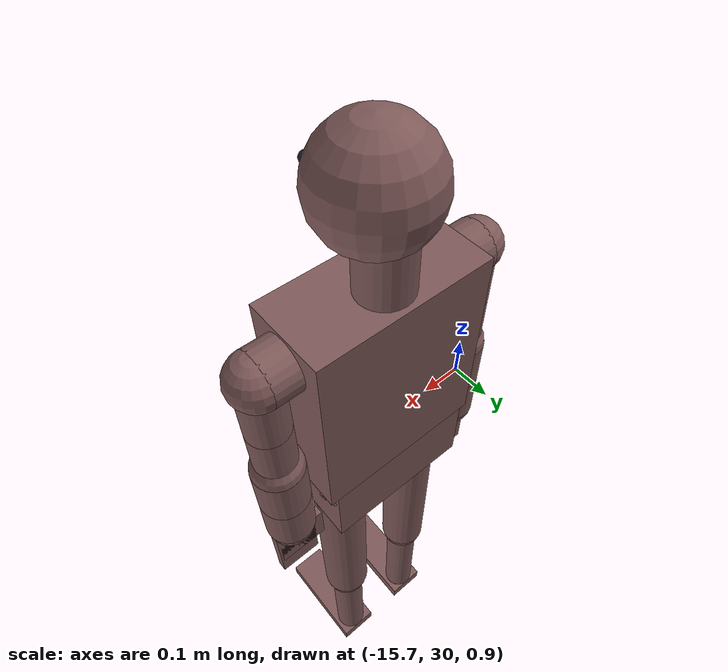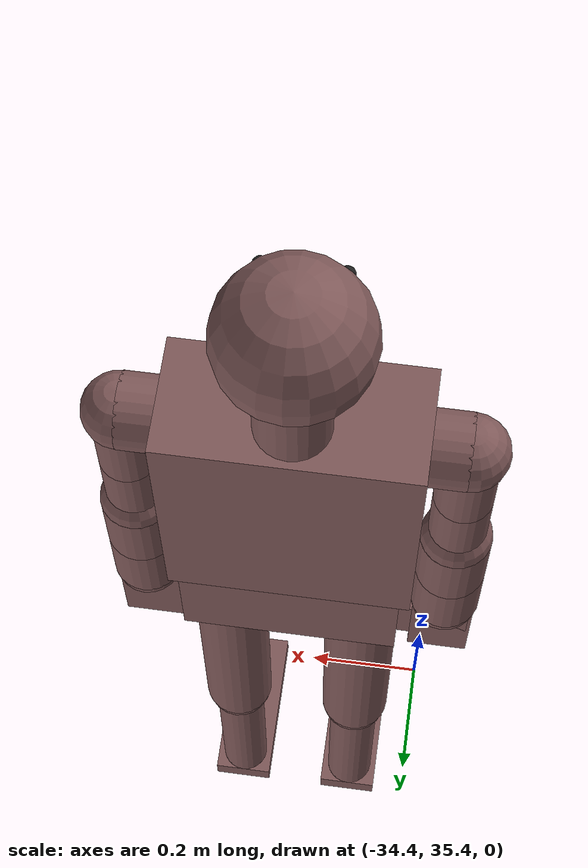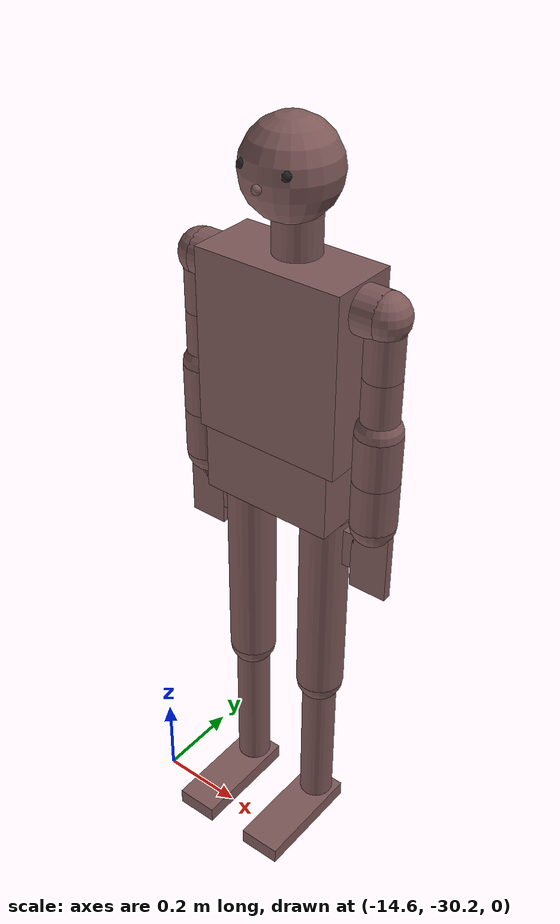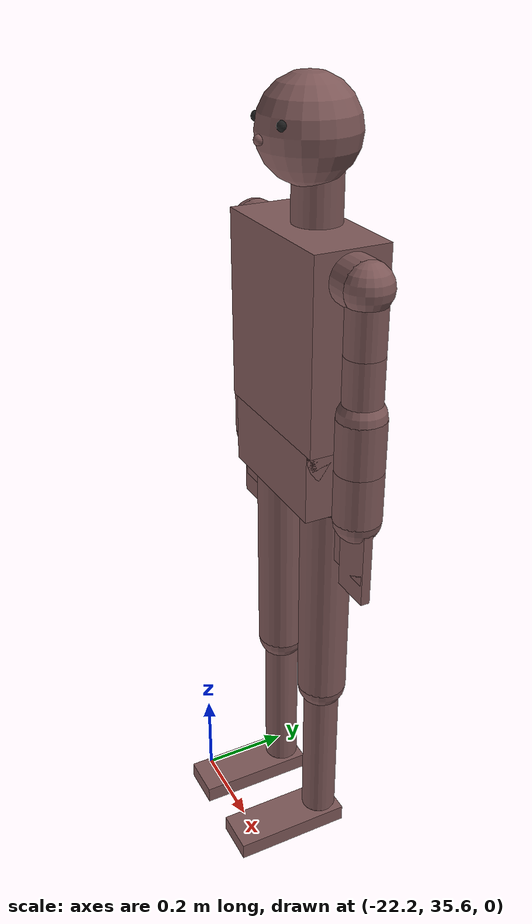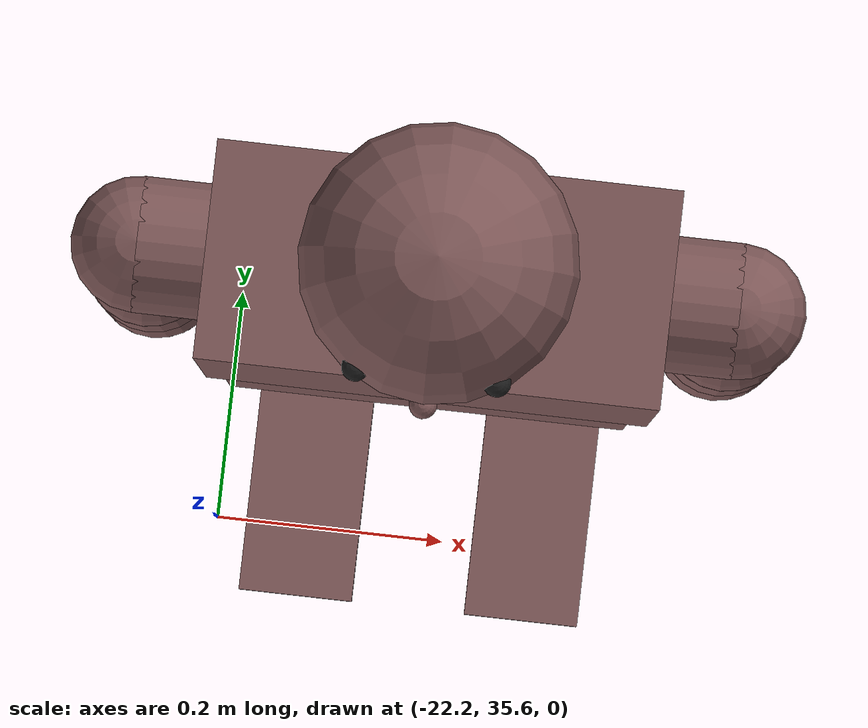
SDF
<sdf version="1.5">
 <world name="default">
  <include><name>victim1</name><pose>-15.3853 30.0694 0 0 -0 0</pose><uri>model://victim175_hot</uri></include>
  <include><name>victim2</name><pose>-34.1968 35.617 0 0 -0 0</pose><uri>model://victim175_hot</uri></include>
  <include><name>victim3</name><pose>-14.344 -30.055 0 0 -0 0</pose><uri>model://victim175_hot</uri></include>
  <include>
   <name>victim4</name>
   <pose>-22.0236 35.7683 0 0 -0 0</pose>
   <uri>model://victim175_hot_moving</uri>
  </include>
  <model name="invisible_ground_plane">
   <static>true</static>
   <link name="link">
    <collision name="collision">
     <geometry><plane><normal>0 0 1</normal><size>5000 5000</size></plane></geometry>
     <surface><friction><ode><mu>1</mu><mu2>1</mu2></ode></friction></surface>
    </collision>
   </link>
  </model>
  <include><uri>model://sun</uri></include>
  <light type="directional" name="SL_TOP">
   <pose>0 0 -100 0 0 0</pose>
   <direction>0 0 1</direction>
   <diffuse>1 1 1 1</diffuse>
   <specular>0.1 0.1 0.1 1</specular>
   <attenuation>
    <range>500</range>
    <linear>0.9</linear>
    <constant>0.5</constant>
    <quadratic>0.1</quadratic>
   </attenuation>
  </light>
  <light type="directional" name="SL_XP">
   <pose>100 0 1 0 0 0</pose>
   <direction>-1 0 0</direction>
   <diffuse>1 1 1 1</diffuse>
   <specular>0.1 0.1 0.1 1</specular>
   <attenuation>
    <range>500</range>
    <linear>0.9</linear>
    <constant>0.5</constant>
    <quadratic>0.1</quadratic>
   </attenuation>
  </light>
  <light type="directional" name="SL_XM">
   <pose>-100 0 1 0 0 0</pose>
   <direction>1 0 0</direction>
   <diffuse>1 1 1 1</diffuse>
   <specular>0.1 0.1 0.1 1</specular>
   <attenuation>
    <range>500</range>
    <linear>0.9</linear>
    <constant>0.5</constant>
    <quadratic>0.1</quadratic>
   </attenuation>
  </light>
  <light type="directional" name="SL_YP">
   <pose>0 100 1 0 0 0</pose>
   <direction>0 -1 0</direction>
   <diffuse>1 1 1 1</diffuse>
   <specular>0.1 0.1 0.1 1</specular>
   <attenuation>
    <range>500</range>
    <linear>0.9</linear>
    <constant>0.5</constant>
    <quadratic>0.1</quadratic>
   </attenuation>
  </light>
  <light type="directional" name="SL_YM">
   <pose>0 -100 1 0 0 0</pose>
   <direction>0 1 0</direction>
   <diffuse>1 1 1 1</diffuse>
   <specular>0.1 0.1 0.1 1</specular>
   <attenuation>
    <range>500</range>
    <linear>0.9</linear>
    <constant>0.5</constant>
    <quadratic>0.1</quadratic>
   </attenuation>
  </light>
 </world>
</sdf>

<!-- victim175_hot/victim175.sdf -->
<sdf version="1.5">
  <model name="victim175_hot">
    <static>true</static>
    <self_collide>true</self_collide>

    <link name="head">
      <pose>0 0 1.625 0 0 0</pose>
      <visual name="visual">
        <pose>0 0 0 0 0 0</pose>
        <geometry>
          <sphere><radius>0.1</radius></sphere>
        </geometry>
        <!-- HOT -->
        <material>
          <emissive>0.5 0.35 0.35 1</emissive>
          <ambient>0.5 0.35 0.35 1</ambient>
          <diffuse>0.5 0.35 0.35 1</diffuse>
          <specular>0 0 0 0</specular>
        </material> -->
      </visual>
      <collision name="collision">
        <pose>0 0 0 0 0 0</pose>
        <geometry>
          <sphere><radius>0.1</radius></sphere>
        </geometry>
      </collision>
      <visual name="visual_nose">
        <pose>0 -0.1 -0.01 0 0 0</pose>
        <geometry>
          <sphere><radius>0.01</radius></sphere>
        </geometry>
        <!-- HOT -->
        <material>
          <emissive>0.5 0.35 0.35 1</emissive>
          <ambient>0.5 0.35 0.35 1</ambient>
          <diffuse>0.5 0.35 0.35 1</diffuse>
          <specular>0 0 0 0</specular>
        </material> -->
      </visual>
      <visual name="visual_rEye">
        <pose>-0.05 -0.08 0.02 0 0 0</pose>
        <geometry>
          <sphere><radius>0.01</radius></sphere>
        </geometry>
        <material>
          <script>
            <uri>file://media/materials/scripts/gazebo.material</uri>
            <name>Gazebo/Black</name>
          </script>
        </material>
      </visual>
      <visual name="visual_lEye">
        <pose>0.05 -0.08 0.02 0 0 0</pose>
        <geometry>
          <sphere><radius>0.01</radius></sphere>
        </geometry>
        <material>
          <script>
            <uri>file://media/materials/scripts/gazebo.material</uri>
            <name>Gazebo/Black</name>
          </script>
        </material>
      </visual>
    </link>

    <link name="neck">
      <pose>0 0.02 1.49 0 0 0</pose>
      <visual name="visual">
        <pose>0 0 0 0 0 0</pose>
        <geometry>
          <cylinder><radius>0.05</radius><length>0.15</length></cylinder>
        </geometry>
        <!-- HOT -->
        <material>
          <emissive>0.5 0.35 0.35 1</emissive>
          <ambient>0.5 0.35 0.35 1</ambient>
          <diffuse>0.5 0.35 0.35 1</diffuse>
          <specular>0 0 0 0</specular>
        </material> -->
      </visual>
      <collision name="collision">
        <pose>0 0 0 0 0 0</pose>
        <geometry>
          <cylinder><radius>0.05</radius><length>0.15</length></cylinder>
        </geometry>
      </collision>
    </link>

    <joint type="revolute" name="neck_head">
      <pose>0 0.02 -0.075 0 0 0</pose>
      <child>head</child>
      <parent>neck</parent>
      <axis>
        <xyz>0 0 -1</xyz>
        <limit>
          <lower>-1.7</lower>
          <upper>+1.7</upper>
        </limit>
        <dynamics>
          <friction>0.01</friction>
        </dynamics>
      </axis>
    </joint>

    <link name="body">
      <pose>0 0 1.255 0 0 0</pose>
      <visual name="visual">
        <pose>0 0 0 0 0 0</pose>
        <geometry>
          <box><size>0.34 0.16 0.4</size></box>
        </geometry>
        <!-- HOT -->
        <material>
          <emissive>0.5 0.35 0.35 1</emissive>
          <ambient>0.5 0.35 0.35 1</ambient>
          <diffuse>0.5 0.35 0.35 1</diffuse>
          <specular>0 0 0 0</specular>
        </material> -->
      </visual>
      <collision name="collision">
        <pose>0 0 0 0 0 0</pose>
        <geometry>
          <box><size>0.34 0.16 0.4</size></box>
        </geometry>
      </collision>
    </link>

    <joint type="revolute" name="body_neck">
      <pose>0 0.06 -0.075 0 0 0</pose>
      <child>neck</child>
      <parent>body</parent>
      <axis>
        <xyz>1 0 0</xyz>
        <limit>
          <lower>-0.2</lower>
          <upper>1</upper>
        </limit>
        <dynamics>
          <friction>0.01</friction>
        </dynamics>
      </axis>
    </joint>

    <link name="waist">
      <pose>0 0 1.005 0 0 0</pose>
      <visual name="visual">
        <pose>0 0 -0.025 0 0 0</pose>
        <geometry>
          <box><size>0.31 0.16 0.15</size></box>
        </geometry>
        <!-- HOT -->
        <material>
          <emissive>0.5 0.35 0.35 1</emissive>
          <ambient>0.5 0.35 0.35 1</ambient>
          <diffuse>0.5 0.35 0.35 1</diffuse>
          <specular>0 0 0 0</specular>
        </material> -->
      </visual>
      <collision name="collision">
        <pose>0 0 0 0 0 0</pose>
        <geometry>
          <box><size>0.31 0.16 0.1</size></box>
        </geometry>
      </collision>
      <visual name="visual2">
        <pose>0 0 0.05 0 1.570796326794897 0</pose>
        <geometry>
          <cylinder><radius>0.08</radius><length>0.31</length></cylinder>
        </geometry>
        <!-- HOT -->
        <material>
          <emissive>0.5 0.35 0.35 1</emissive>
          <ambient>0.5 0.35 0.35 1</ambient>
          <diffuse>0.5 0.35 0.35 1</diffuse>
          <specular>0 0 0 0</specular>
        </material> -->
      </visual>
      <collision name="collision2">
        <pose>0 0 0.05 0 1.570796326794897 0</pose>
        <geometry>
          <cylinder><radius>0.08</radius><length>0.31</length></cylinder>
        </geometry>
      </collision>
    </link>

    <joint type="revolute" name="body_waist">
      <pose>0 0 0.05 0 0 0</pose>
      <child>waist</child>
      <parent>body</parent>
      <axis>
        <xyz>-1 0 0</xyz>
        <limit>
          <lower>0</lower>
          <upper>0</upper>
        </limit>
        <dynamics>
          <friction>0.01</friction>
        </dynamics>
      </axis>
    </joint>

    <link name="rHand">
      <pose>-0.22 0 0.84 0 0 0</pose>
      <visual name="visual">
        <pose>0 0 0 0 0 0</pose>
        <geometry>
          <box><size>0.09 0.02 0.18</size></box>
        </geometry>
        <!-- HOT -->
        <material>
          <emissive>0.5 0.35 0.35 1</emissive>
          <ambient>0.5 0.35 0.35 1</ambient>
          <diffuse>0.5 0.35 0.35 1</diffuse>
          <specular>0 0 0 0</specular>
        </material> -->
      </visual>
      <collision name="collision">
        <pose>0 0 0 0 0 0</pose>
        <geometry>
          <box><size>0.09 0.02 0.18</size></box>
        </geometry>
      </collision>
      <visual name="visual2">
        <pose>0.02 0 0 0 0 0</pose>
        <geometry>
          <box><size>0.12 0.02 0.09</size></box>
        </geometry>
        <!-- HOT -->
        <material>
          <emissive>0.5 0.35 0.35 1</emissive>
          <ambient>0.5 0.35 0.35 1</ambient>
          <diffuse>0.5 0.35 0.35 1</diffuse>
          <specular>0 0 0 0</specular>
        </material> -->
      </visual>
      <collision name="collision2">
        <pose>0.02 0 0 0 0 0</pose>
        <geometry>
          <box><size>0.12 0.02 0.09</size></box>
        </geometry>
      </collision>
    </link>

    <link name="lHand">
      <pose>0.22 0 0.84 0 0 0</pose>
      <visual name="visual">
        <pose>0 0 0 0 0 0</pose>
        <geometry>
          <box><size>0.09 0.02 0.18</size></box>
        </geometry>
        <!-- HOT -->
        <material>
          <emissive>0.5 0.35 0.35 1</emissive>
          <ambient>0.5 0.35 0.35 1</ambient>
          <diffuse>0.5 0.35 0.35 1</diffuse>
          <specular>0 0 0 0</specular>
        </material> -->
      </visual>
      <collision name="collision">
        <pose>0 0 0 0 0 0</pose>
        <geometry>
          <box><size>0.09 0.02 0.18</size></box>
        </geometry>
      </collision>
      <visual name="visual2">
        <pose>-0.02 0 0 0 0 0</pose>
        <geometry>
          <box><size>0.12 0.02 0.09</size></box>
        </geometry>
        <!-- HOT -->
        <material>
          <emissive>0.5 0.35 0.35 1</emissive>
          <ambient>0.5 0.35 0.35 1</ambient>
          <diffuse>0.5 0.35 0.35 1</diffuse>
          <specular>0 0 0 0</specular>
        </material> -->
      </visual>
      <collision name="collision2">
        <pose>-0.02 0 0 0 0 0</pose>
        <geometry>
          <box><size>0.12 0.02 0.09</size></box>
        </geometry>
      </collision>
    </link>

    <link name="rFoot">
      <pose>-0.1 -0.095 0.02 0 0 0</pose>
      <visual name="visual">
        <pose>0 0 0 0 0 0</pose>
        <geometry>
          <box><size>0.1 0.27 0.04</size></box>
        </geometry>
        <!-- HOT -->
        <material>
          <emissive>0.5 0.35 0.35 1</emissive>
          <ambient>0.5 0.35 0.35 1</ambient>
          <diffuse>0.5 0.35 0.35 1</diffuse>
          <specular>0 0 0 0</specular>
        </material> -->
      </visual>
      <collision name="collision">
        <pose>0 0 0 0 0 0</pose>
        <geometry>
          <box><size>0.1 0.27 0.04</size></box>
        </geometry>
      </collision>
    </link>

    <link name="lFoot">
      <pose>0.1 -0.095 0.02 0 0 0</pose>
      <visual name="visual">
        <pose>0 0 0 0 0 0</pose>
        <geometry>
          <box><size>0.1 0.27 0.04</size></box>
        </geometry>
        <!-- HOT -->
        <material>
          <emissive>0.5 0.35 0.35 1</emissive>
          <ambient>0.5 0.35 0.35 1</ambient>
          <diffuse>0.5 0.35 0.35 1</diffuse>
          <specular>0 0 0 0</specular>
        </material> -->
      </visual>
      <collision name="collision">
        <pose>0 0 0 0 0 0</pose>
        <geometry>
          <box><size>0.1 0.27 0.04</size></box>
        </geometry>
      </collision>
    </link>

    <link name="rLeg2">
      <pose>-0.1 0 0.23 0 0 0</pose>
      <visual name="visual">
        <pose>0 0 0 0 0 0</pose>
        <geometry>
          <cylinder><radius>0.04</radius><length>0.38</length></cylinder>
        </geometry>
        <!-- HOT -->
        <material>
          <emissive>0.5 0.35 0.35 1</emissive>
          <ambient>0.5 0.35 0.35 1</ambient>
          <diffuse>0.5 0.35 0.35 1</diffuse>
          <specular>0 0 0 0</specular>
        </material> -->
      </visual>
      <collision name="collision">
        <pose>0 0 0 0 0 0</pose>
        <geometry>
          <cylinder><radius>0.04</radius><length>0.38</length></cylinder>
        </geometry>
      </collision>
      <visual name="visual2">
        <pose>0 0 -0.19 0 0 0</pose>
        <geometry>
          <sphere><radius>0.04</radius></sphere>
        </geometry>
        <!-- HOT -->
        <material>
          <emissive>0.5 0.35 0.35 1</emissive>
          <ambient>0.5 0.35 0.35 1</ambient>
          <diffuse>0.5 0.35 0.35 1</diffuse>
          <specular>0 0 0 0</specular>
        </material> -->
      </visual>
      <collision name="collision2">
        <pose>0 0 -0.19 0 0 0</pose>
        <geometry>
          <sphere><radius>0.04</radius></sphere>
        </geometry>
      </collision>
    </link>

    <link name="lLeg2">
      <pose>0.1 0 0.23 0 0 0</pose>
      <visual name="visual">
        <pose>0 0 0 0 0 0</pose>
        <geometry>
          <cylinder><radius>0.04</radius><length>0.38</length></cylinder>
        </geometry>
        <!-- HOT -->
        <material>
          <emissive>0.5 0.35 0.35 1</emissive>
          <ambient>0.5 0.35 0.35 1</ambient>
          <diffuse>0.5 0.35 0.35 1</diffuse>
          <specular>0 0 0 0</specular>
        </material> -->
      </visual>
      <collision name="collision">
        <pose>0 0 0 0 0 0</pose>
        <geometry>
          <cylinder><radius>0.04</radius><length>0.38</length></cylinder>
        </geometry>
      </collision>
      <visual name="visual2">
        <pose>0 0 -0.19 0 0 0</pose>
        <geometry>
          <sphere><radius>0.04</radius></sphere>
        </geometry>
        <!-- HOT -->
        <material>
          <emissive>0.5 0.35 0.35 1</emissive>
          <ambient>0.5 0.35 0.35 1</ambient>
          <diffuse>0.5 0.35 0.35 1</diffuse>
          <specular>0 0 0 0</specular>
        </material> -->
      </visual>
      <collision name="collision2">
        <pose>0 0 -0.19 0 0 0</pose>
        <geometry>
          <sphere><radius>0.04</radius></sphere>
        </geometry>
      </collision>
    </link>

    <joint type="revolute" name="rLeg2_rFoot">
      <pose>0 0.095 0.02 0 0 0</pose>
      <child>rFoot</child>
      <parent>rLeg2</parent>
      <axis>
        <xyz>1 0 0</xyz>
        <limit>
          <lower>0</lower>
          <upper>0</upper>
        </limit>
        <dynamics>
          <friction>0.01</friction>
        </dynamics>
      </axis>
    </joint>

    <joint type="revolute" name="lLeg2_lFoot">
      <pose>0 0.095 0.02 0 0 0</pose>
      <child>lFoot</child>
      <parent>lLeg2</parent>
      <axis>
        <xyz>1 0 0</xyz>
        <limit>
          <lower>0</lower>
          <upper>0</upper>
        </limit>
        <dynamics>
          <friction>0.01</friction>
        </dynamics>
      </axis>
    </joint>

    <link name="rLeg1">
      <pose>-0.1 0 0.66 0 0 0</pose>
      <visual name="visual">
        <pose>0 0 0 0 0 0</pose>
        <geometry>
          <cylinder><radius>0.055</radius><length>0.48</length></cylinder>
        </geometry>
        <!-- HOT -->
        <material>
          <emissive>0.5 0.35 0.35 1</emissive>
          <ambient>0.5 0.35 0.35 1</ambient>
          <diffuse>0.5 0.35 0.35 1</diffuse>
          <specular>0 0 0 0</specular>
        </material> -->
      </visual>
      <collision name="collision">
        <pose>0 0 0 0 0 0</pose>
        <geometry>
          <cylinder><radius>0.055</radius><length>0.48</length></cylinder>
        </geometry>
      </collision>
      <visual name="visual2">
        <pose>0 0 -0.24 0 0 0</pose>
        <geometry>
          <sphere><radius>0.055</radius></sphere>
        </geometry>
        <!-- HOT -->
        <material>
          <emissive>0.5 0.35 0.35 1</emissive>
          <ambient>0.5 0.35 0.35 1</ambient>
          <diffuse>0.5 0.35 0.35 1</diffuse>
          <specular>0 0 0 0</specular>
        </material> -->
      </visual>
      <collision name="collision2">
        <pose>0 0 -0.24 0 0 0</pose>
        <geometry>
          <sphere><radius>0.055</radius></sphere>
        </geometry>
      </collision>
      <visual name="visual3">
        <pose>0 0 0.24 0 0 0</pose>
        <geometry>
          <sphere><radius>0.055</radius></sphere>
        </geometry>
        <!-- HOT -->
        <material>
          <emissive>0.5 0.35 0.35 1</emissive>
          <ambient>0.5 0.35 0.35 1</ambient>
          <diffuse>0.5 0.35 0.35 1</diffuse>
          <specular>0 0 0 0</specular>
        </material> -->
      </visual>
      <collision name="collision3">
        <pose>0 0 0.24 0 0 0</pose>
        <geometry>
          <sphere><radius>0.055</radius></sphere>
        </geometry>
      </collision>
    </link>

    <link name="lLeg1">
      <pose>0.1 0 0.66 0 0 0</pose>
      <visual name="visual">
        <pose>0 0 0 0 0 0</pose>
        <geometry>
          <cylinder><radius>0.055</radius><length>0.48</length></cylinder>
        </geometry>
        <!-- HOT -->
        <material>
          <emissive>0.5 0.35 0.35 1</emissive>
          <ambient>0.5 0.35 0.35 1</ambient>
          <diffuse>0.5 0.35 0.35 1</diffuse>
          <specular>0 0 0 0</specular>
        </material> -->
      </visual>
      <collision name="collision">
        <pose>0 0 0 0 0 0</pose>
        <geometry>
          <cylinder><radius>0.055</radius><length>0.48</length></cylinder>
        </geometry>
      </collision>
      <visual name="visual2">
        <pose>0 0 -0.24 0 0 0</pose>
        <geometry>
          <sphere><radius>0.055</radius></sphere>
        </geometry>
        <!-- HOT -->
        <material>
          <emissive>0.5 0.35 0.35 1</emissive>
          <ambient>0.5 0.35 0.35 1</ambient>
          <diffuse>0.5 0.35 0.35 1</diffuse>
          <specular>0 0 0 0</specular>
        </material> -->
      </visual>
      <collision name="collision2">
        <pose>0 0 -0.24 0 0 0</pose>
        <geometry>
          <sphere><radius>0.055</radius></sphere>
        </geometry>
      </collision>
      <visual name="visual3">
        <pose>0 0 0.24 0 0 0</pose>
        <geometry>
          <sphere><radius>0.055</radius></sphere>
        </geometry>
        <!-- HOT -->
        <material>
          <emissive>0.5 0.35 0.35 1</emissive>
          <ambient>0.5 0.35 0.35 1</ambient>
          <diffuse>0.5 0.35 0.35 1</diffuse>
          <specular>0 0 0 0</specular>
        </material> -->
      </visual>
      <collision name="collision3">
        <pose>0 0 0.24 0 0 0</pose>
        <geometry>
          <sphere><radius>0.055</radius></sphere>
        </geometry>
      </collision>
    </link>

    <joint type="revolute" name="rLeg1_rLeg2">
      <pose>0 0 0.19 0 0 0</pose>
      <child>rLeg2</child>
      <parent>rLeg1</parent>
      <axis>
        <xyz>1 0 0</xyz>
        <limit>
          <lower>0</lower>
          <upper>0</upper>
        </limit>
        <dynamics>
          <friction>0.01</friction>
        </dynamics>
      </axis>
    </joint>

    <joint type="revolute" name="lLeg1_lLeg2">
      <pose>0 0 0.19 0 0 0</pose>
      <child>lLeg2</child>
      <parent>lLeg1</parent>
      <axis>
        <xyz>1 0 0</xyz>
        <limit>
          <lower>0</lower>
          <upper>0</upper>
        </limit>
        <dynamics>
          <friction>0.01</friction>
        </dynamics>
      </axis>
    </joint>

    <link name="rButt">
      <pose>-0.1 0 0.9275 0 0 0</pose>
      <visual name="visual">
        <pose>0 0 0 0 0 0</pose>
        <geometry>
          <cylinder><radius>0.055</radius><length>0.055</length></cylinder>
        </geometry>
        <!-- HOT -->
        <material>
          <emissive>0.5 0.35 0.35 1</emissive>
          <ambient>0.5 0.35 0.35 1</ambient>
          <diffuse>0.5 0.35 0.35 1</diffuse>
          <specular>0 0 0 0</specular>
        </material> -->
      </visual>
      <collision name="collision">
        <pose>0 0 0 0 0 0</pose>
        <geometry>
          <cylinder><radius>0.055</radius><length>0.055</length></cylinder>
        </geometry>
      </collision>
    </link>

    <link name="lButt">
      <pose>0.1 0 0.9275 0 0 0</pose>
      <visual name="visual">
        <pose>0 0 0 0 0 0</pose>
        <geometry>
          <cylinder><radius>0.055</radius><length>0.055</length></cylinder>
        </geometry>
        <!-- HOT -->
        <material>
          <emissive>0.5 0.35 0.35 1</emissive>
          <ambient>0.5 0.35 0.35 1</ambient>
          <diffuse>0.5 0.35 0.35 1</diffuse>
          <specular>0 0 0 0</specular>
        </material> -->
      </visual>
      <collision name="collision">
        <pose>0 0 0 0 0 0</pose>
        <geometry>
          <cylinder><radius>0.055</radius><length>0.055</length></cylinder>
        </geometry>
      </collision>
    </link>

    <joint type="revolute" name="rButt_rLeg1">
      <pose>0 0 0.24 0 0 0</pose>
      <child>rLeg1</child>
      <parent>rButt</parent>
      <axis>
        <xyz>1 0 0</xyz>
        <limit>
          <lower>0</lower>
          <upper>0</upper>
        </limit>
        <dynamics>
          <friction>0.01</friction>
        </dynamics>
      </axis>
    </joint>

    <joint type="revolute" name="lButt_lLeg1">
      <pose>0 0 0.24 0 0 0</pose>
      <child>lLeg1</child>
      <parent>lButt</parent>
      <axis>
        <xyz>1 0 0</xyz>
        <limit>
          <lower>0</lower>
          <upper>0</upper>
        </limit>
        <dynamics>
          <friction>0.01</friction>
        </dynamics>
      </axis>
    </joint>

    <joint type="revolute" name="waist_rButt">
      <pose>0 0 0 0 0 0</pose>
      <child>rButt</child>
      <parent>waist</parent>
      <axis>
        <xyz>0 0 -1</xyz>
        <limit>
          <lower>-1</lower>
          <upper>+1</upper>
        </limit>
        <dynamics>
          <friction>0.01</friction>
        </dynamics>
      </axis>
    </joint>

    <joint type="revolute" name="waist_lButt">
      <pose>0 0 0 0 0 0</pose>
      <child>lButt</child>
      <parent>waist</parent>
      <axis>
        <xyz>0 0 1</xyz>
        <limit>
          <lower>-1</lower>
          <upper>+1</upper>
        </limit>
        <dynamics>
          <friction>0.01</friction>
        </dynamics>
      </axis>
    </joint>

    <link name="rShoulder">
      <pose>-0.195 0 1.4 0 0 0</pose>
      <visual name="visual">
        <pose>0 0 0 0 1.570796326794897 0</pose>
        <geometry>
          <cylinder><radius>0.05</radius><length>0.05</length></cylinder>
        </geometry>
        <!-- HOT -->
        <material>
          <emissive>0.5 0.35 0.35 1</emissive>
          <ambient>0.5 0.35 0.35 1</ambient>
          <diffuse>0.5 0.35 0.35 1</diffuse>
          <specular>0 0 0 0</specular>
        </material> -->
      </visual>
      <collision name="collision">
        <pose>0 0 0 0 1.570796326794897 0</pose>
        <geometry>
          <cylinder><radius>0.05</radius><length>0.05</length></cylinder>
        </geometry>
      </collision>
    </link>

    <link name="lShoulder">
      <pose>0.195 0 1.4 0 0 0</pose>
      <visual name="visual">
        <pose>0 0 0 0 1.570796326794897 0</pose>
        <geometry>
          <cylinder><radius>0.05</radius><length>0.05</length></cylinder>
        </geometry>
        <!-- HOT -->
        <material>
          <emissive>0.5 0.35 0.35 1</emissive>
          <ambient>0.5 0.35 0.35 1</ambient>
          <diffuse>0.5 0.35 0.35 1</diffuse>
          <specular>0 0 0 0</specular>
        </material> -->
      </visual>
      <collision name="collision">
        <pose>0 0 0 0 1.570796326794897 0</pose>
        <geometry>
          <cylinder><radius>0.05</radius><length>0.05</length></cylinder>
        </geometry>
      </collision>
    </link>

    <joint type="revolute" name="body_rShoulder">
      <pose>0 0 0 0 0 0</pose>
      <child>rShoulder</child>
      <parent>body</parent>
      <axis>
        <xyz>-1 0 0</xyz>
        <limit>
          <lower>-1.570796326794897</lower>
          <upper>+3.2</upper>
        </limit>
        <dynamics>
          <friction>0.01</friction>
        </dynamics>
      </axis>
    </joint>

    <joint type="revolute" name="body_lShoulder">
      <pose>0 0 0 0 0 0</pose>
      <child>lShoulder</child>
      <parent>body</parent>
      <axis>
        <xyz>1 0 0</xyz>
        <limit>
          <lower>-1.570796326794897</lower>
          <upper>+3.2</upper>
        </limit>
        <dynamics>
          <friction>0.01</friction>
        </dynamics>
      </axis>
    </joint>

    <link name="rArm1U">
      <pose>-0.22 0 1.3375 0 0 0</pose>
      <visual name="visual">
        <pose>0 0 0 0 0 0</pose>
        <geometry>
          <cylinder><radius>0.04</radius><length>0.125</length></cylinder>
        </geometry>
        <!-- HOT -->
        <material>
          <emissive>0.5 0.35 0.35 1</emissive>
          <ambient>0.5 0.35 0.35 1</ambient>
          <diffuse>0.5 0.35 0.35 1</diffuse>
          <specular>0 0 0 0</specular>
        </material> -->
      </visual>
      <collision name="collision">
        <pose>0 0 0 0 0 0</pose>
        <geometry>
          <cylinder><radius>0.04</radius><length>0.125</length></cylinder>
        </geometry>
      </collision>
      <visual name="visual2">
        <pose>0 0 0.0625 0 0 0</pose>
        <geometry>
          <sphere><radius>0.05</radius></sphere>
        </geometry>
        <!-- HOT -->
        <material>
          <emissive>0.5 0.35 0.35 1</emissive>
          <ambient>0.5 0.35 0.35 1</ambient>
          <diffuse>0.5 0.35 0.35 1</diffuse>
          <specular>0 0 0 0</specular>
        </material> -->
      </visual>
      <collision name="collision2">
        <pose>0 0 0.0625 0 0 0</pose>
        <geometry>
          <sphere><radius>0.05</radius></sphere>
        </geometry>
      </collision>
    </link>

    <link name="rArm1L">
      <pose>-0.22 0 1.2125 0 0 0</pose>
      <visual name="visual">
        <pose>0 0 0 0 0 0</pose>
        <geometry>
          <cylinder><radius>0.04</radius><length>0.125</length></cylinder>
        </geometry>
        <!-- HOT -->
        <material>
          <emissive>0.5 0.35 0.35 1</emissive>
          <ambient>0.5 0.35 0.35 1</ambient>
          <diffuse>0.5 0.35 0.35 1</diffuse>
          <specular>0 0 0 0</specular>
        </material> -->
      </visual>
      <collision name="collision">
        <pose>0 0 0 0 0 0</pose>
        <geometry>
          <cylinder><radius>0.04</radius><length>0.125</length></cylinder>
        </geometry>
      </collision>
      <visual name="visual2">
        <pose>0 0 -0.0625 0 0 0</pose>
        <geometry>
          <sphere><radius>0.05</radius></sphere>
        </geometry>
        <!-- HOT -->
        <material>
          <emissive>0.5 0.35 0.35 1</emissive>
          <ambient>0.5 0.35 0.35 1</ambient>
          <diffuse>0.5 0.35 0.35 1</diffuse>
          <specular>0 0 0 0</specular>
        </material> -->
      </visual>
      <collision name="collision2">
        <pose>0 0 -0.0625 0 0 0</pose>
        <geometry>
          <sphere><radius>0.05</radius></sphere>
        </geometry>
      </collision>
    </link>

    <joint type="revolute" name="rArm1U_rArm1L">
      <pose>0 0 0.0625 0 0 0</pose>
      <child>rArm1L</child>
      <parent>rArm1U</parent>
      <axis>
        <xyz>0 0 -1</xyz>
        <limit>
          <lower>-1.570796326794897</lower>
          <upper>+1.570796326794897</upper>
        </limit>
        <dynamics>
          <friction>0.01</friction>
        </dynamics>
      </axis>
    </joint>

    <link name="lArm1U">
      <pose>0.22 0 1.3375 0 0 0</pose>
      <visual name="visual">
        <pose>0 0 0 0 0 0</pose>
        <geometry>
          <cylinder><radius>0.04</radius><length>0.125</length></cylinder>
        </geometry>
        <!-- HOT -->
        <material>
          <emissive>0.5 0.35 0.35 1</emissive>
          <ambient>0.5 0.35 0.35 1</ambient>
          <diffuse>0.5 0.35 0.35 1</diffuse>
          <specular>0 0 0 0</specular>
        </material> -->
      </visual>
      <collision name="collision">
        <pose>0 0 0 0 0 0</pose>
        <geometry>
          <cylinder><radius>0.04</radius><length>0.125</length></cylinder>
        </geometry>
      </collision>
      <visual name="visual2">
        <pose>0 0 0.0625 0 0 0</pose>
        <geometry>
          <sphere><radius>0.05</radius></sphere>
        </geometry>
        <!-- HOT -->
        <material>
          <emissive>0.5 0.35 0.35 1</emissive>
          <ambient>0.5 0.35 0.35 1</ambient>
          <diffuse>0.5 0.35 0.35 1</diffuse>
          <specular>0 0 0 0</specular>
        </material> -->
      </visual>
      <collision name="collision2">
        <pose>0 0 0.0625 0 0 0</pose>
        <geometry>
          <sphere><radius>0.05</radius></sphere>
        </geometry>
      </collision>
    </link>

    <link name="lArm1L">
      <pose>0.22 0 1.2125 0 0 0</pose>
      <visual name="visual">
        <pose>0 0 0 0 0 0</pose>
        <geometry>
          <cylinder><radius>0.04</radius><length>0.125</length></cylinder>
        </geometry>
        <!-- HOT -->
        <material>
          <emissive>0.5 0.35 0.35 1</emissive>
          <ambient>0.5 0.35 0.35 1</ambient>
          <diffuse>0.5 0.35 0.35 1</diffuse>
          <specular>0 0 0 0</specular>
        </material> -->
      </visual>
      <collision name="collision">
        <pose>0 0 0 0 0 0</pose>
        <geometry>
          <cylinder><radius>0.04</radius><length>0.125</length></cylinder>
        </geometry>
      </collision>
      <visual name="visual2">
        <pose>0 0 -0.0625 0 0 0</pose>
        <geometry>
          <sphere><radius>0.05</radius></sphere>
        </geometry>
        <!-- HOT -->
        <material>
          <emissive>0.5 0.35 0.35 1</emissive>
          <ambient>0.5 0.35 0.35 1</ambient>
          <diffuse>0.5 0.35 0.35 1</diffuse>
          <specular>0 0 0 0</specular>
        </material> -->
      </visual>
      <collision name="collision2">
        <pose>0 0 -0.0625 0 0 0</pose>
        <geometry>
          <sphere><radius>0.05</radius></sphere>
        </geometry>
      </collision>
    </link>

    <joint type="revolute" name="lArm1U_lArm1L">
      <pose>0 0 0.0625 0 0 0</pose>
      <child>lArm1L</child>
      <parent>lArm1U</parent>
      <axis>
        <xyz>0 0 1</xyz>
        <limit>
          <lower>-1.570796326794897</lower>
          <upper>+1.570796326794897</upper>
        </limit>
        <dynamics>
          <friction>0.01</friction>
        </dynamics>
      </axis>
    </joint>

    <joint type="revolute" name="rShoulder_rArm1">
      <pose>0 0 0.0625 0 0 0</pose>
      <child>rArm1U</child>
      <parent>rShoulder</parent>
      <axis>
        <xyz>0 -1 0</xyz>
        <limit>
          <lower>-1.570796326794897</lower>
          <upper>+3.2</upper>
        </limit>
        <dynamics>
          <friction>0.01</friction>
        </dynamics>
      </axis>
    </joint>

    <joint type="revolute" name="lShoulder_lArm1">
      <pose>0 0 0.0625 0 0 0</pose>
      <child>lArm1U</child>
      <parent>lShoulder</parent>
      <axis>
        <xyz>0 1 0</xyz>
        <limit>
          <lower>-1.570796326794897</lower>
          <upper>+3.2</upper>
        </limit>
        <dynamics>
          <friction>0.01</friction>
        </dynamics>
      </axis>
    </joint>

    <link name="rArm2U">
      <pose>-0.22 0 1.095 0 0 0</pose>
      <visual name="visual">
        <pose>0 0 0 0 0 0</pose>
        <geometry>
          <cylinder><radius>0.05</radius><length>0.11</length></cylinder>
        </geometry>
        <!-- HOT -->
        <material>
          <emissive>0.5 0.35 0.35 1</emissive>
          <ambient>0.5 0.35 0.35 1</ambient>
          <diffuse>0.5 0.35 0.35 1</diffuse>
          <specular>0 0 0 0</specular>
        </material> -->
      </visual>
      <collision name="collision">
        <pose>0 0 0 0 0 0</pose>
        <geometry>
          <cylinder><radius>0.05</radius><length>0.11</length></cylinder>
        </geometry>
      </collision>
    </link>

    <link name="rArm2L">
      <pose>-0.22 0 0.985 0 0 0</pose>
      <visual name="visual">
        <pose>0 0 0 0 0 0</pose>
        <geometry>
          <cylinder><radius>0.05</radius><length>0.11</length></cylinder>
        </geometry>
        <!-- HOT -->
        <material>
          <emissive>0.5 0.35 0.35 1</emissive>
          <ambient>0.5 0.35 0.35 1</ambient>
          <diffuse>0.5 0.35 0.35 1</diffuse>
          <specular>0 0 0 0</specular>
        </material> -->
      </visual>
      <collision name="collision">
        <pose>0 0 0 0 0 0</pose>
        <geometry>
          <cylinder><radius>0.05</radius><length>0.11</length></cylinder>
        </geometry>
      </collision>
      <visual name="visual2">
        <pose>0 0 -0.055 0 0 0</pose>
        <geometry>
          <sphere><radius>0.05</radius></sphere>
        </geometry>
        <!-- HOT -->
        <material>
          <emissive>0.5 0.35 0.35 1</emissive>
          <ambient>0.5 0.35 0.35 1</ambient>
          <diffuse>0.5 0.35 0.35 1</diffuse>
          <specular>0 0 0 0</specular>
        </material> -->
      </visual>
      <collision name="collision2">
        <pose>0 0 -0.055 0 0 0</pose>
        <geometry>
          <sphere><radius>0.05</radius></sphere>
        </geometry>
      </collision>
    </link>

    <joint type="revolute" name="rArm2U_rArm2L">
      <pose>0 0 0.055 0 0 0</pose>
      <child>rArm2L</child>
      <parent>rArm2U</parent>
      <axis>
        <xyz>0 0 -1</xyz>
        <limit>
          <lower>-1.570796326794897</lower>
          <upper>+1.570796326794897</upper>
        </limit>
        <dynamics>
          <friction>0.01</friction>
        </dynamics>
      </axis>
    </joint>

    <link name="lArm2U">
      <pose>0.22 0 1.095 0 0 0</pose>
      <visual name="visual">
        <pose>0 0 0 0 0 0</pose>
        <geometry>
          <cylinder><radius>0.05</radius><length>0.11</length></cylinder>
        </geometry>
        <!-- HOT -->
        <material>
          <emissive>0.5 0.35 0.35 1</emissive>
          <ambient>0.5 0.35 0.35 1</ambient>
          <diffuse>0.5 0.35 0.35 1</diffuse>
          <specular>0 0 0 0</specular>
        </material> -->
      </visual>
      <collision name="collision">
        <pose>0 0 0 0 0 0</pose>
        <geometry>
          <cylinder><radius>0.05</radius><length>0.11</length></cylinder>
        </geometry>
      </collision>
    </link>

    <link name="lArm2L">
      <pose>0.22 0 0.985 0 0 0</pose>
      <visual name="visual">
        <pose>0 0 0 0 0 0</pose>
        <geometry>
          <cylinder><radius>0.05</radius><length>0.11</length></cylinder>
        </geometry>
        <!-- HOT -->
        <material>
          <emissive>0.5 0.35 0.35 1</emissive>
          <ambient>0.5 0.35 0.35 1</ambient>
          <diffuse>0.5 0.35 0.35 1</diffuse>
          <specular>0 0 0 0</specular>
        </material> -->
      </visual>
      <collision name="collision">
        <pose>0 0 0 0 0 0</pose>
        <geometry>
          <cylinder><radius>0.05</radius><length>0.11</length></cylinder>
        </geometry>
      </collision>
      <visual name="visual2">
        <pose>0 0 -0.055 0 0 0</pose>
        <geometry>
          <sphere><radius>0.05</radius></sphere>
        </geometry>
        <!-- HOT -->
        <material>
          <emissive>0.5 0.35 0.35 1</emissive>
          <ambient>0.5 0.35 0.35 1</ambient>
          <diffuse>0.5 0.35 0.35 1</diffuse>
          <specular>0 0 0 0</specular>
        </material> -->
      </visual>
      <collision name="collision2">
        <pose>0 0 -0.055 0 0 0</pose>
        <geometry>
          <sphere><radius>0.05</radius></sphere>
        </geometry>
      </collision>
    </link>

    <joint type="revolute" name="lArm2U_lArm2L">
      <pose>0 0 0.055 0 0 0</pose>
      <child>lArm2L</child>
      <parent>lArm2U</parent>
      <axis>
        <xyz>0 0 1</xyz>
        <limit>
          <lower>-1.570796326794897</lower>
          <upper>+1.570796326794897</upper>
        </limit>
        <dynamics>
          <friction>0.01</friction>
        </dynamics>
      </axis>
    </joint>

    <joint type="revolute" name="rArm1_rArm2">
      <pose>0 0 0.055 0 0 0</pose>
      <child>rArm2U</child>
      <parent>rArm1L</parent>
      <axis>
        <xyz>-1 0 0</xyz>
        <limit>
          <lower>0</lower>
          <upper>2.8</upper>
        </limit>
        <dynamics>
          <friction>0.01</friction>
        </dynamics>
      </axis>
    </joint>

    <joint type="revolute" name="lArm1_lArm2">
      <pose>0 0 0.055 0 0 0</pose>
      <child>lArm2U</child>
      <parent>lArm1L</parent>
      <axis>
        <xyz>-1 0 0</xyz>
        <limit>
          <lower>0</lower>
          <upper>2.8</upper>
        </limit>
        <dynamics>
          <friction>0.01</friction>
        </dynamics>
      </axis>
    </joint>

    <joint type="revolute" name="rArm2_rHand">
      <pose>0 0 0.09 0 0 0</pose>
      <child>rHand</child>
      <parent>rArm2L</parent>
      <axis>
        <xyz>-1 0 0</xyz>
        <limit>
          <lower>-1.57</lower>
          <upper>1.4</upper>
        </limit>
        <dynamics>
          <friction>0.01</friction>
        </dynamics>
      </axis>
    </joint>

    <joint type="revolute" name="lArm2_lHand">
      <pose>0 0 0.09 0 0 0</pose>
      <child>lHand</child>
      <parent>lArm2L</parent>
      <axis>
        <xyz>-1 0 0</xyz>
        <limit>
          <lower>-1.57</lower>
          <upper>1.4</upper>
        </limit>
        <dynamics>
          <friction>0.01</friction>
        </dynamics>
      </axis>
    </joint>

    <joint type="revolute" name="world_rFoot">
      <pose>0 0 0 0 0 0</pose>
      <child>rFoot</child>
      <parent>world</parent>
      <axis>
        <xyz>0 0 1</xyz>
        <limit>
          <lower>0</lower>
          <upper>0</upper>
        </limit>
      </axis>
    </joint>

    <joint type="revolute" name="world_lFoot">
      <pose>0 0 0 0 0 0</pose>
      <child>lFoot</child>
      <parent>world</parent>
      <axis>
        <xyz>0 0 1</xyz>
        <limit>
          <lower>0</lower>
          <upper>0</upper>
        </limit>
      </axis>
    </joint>
  </model>
</sdf>

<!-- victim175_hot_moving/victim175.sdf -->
<sdf version="1.5">
  <model name="victim175_hot_moving">
    <static>true</static>
    <self_collide>true</self_collide>

    <link name="head">
      <pose>0 0 1.625 0 0 0</pose>
      <visual name="visual">
        <pose>0 0 0 0 0 0</pose>
        <geometry>
          <sphere><radius>0.1</radius></sphere>
        </geometry>
        <!-- HOT -->
        <material>
          <emissive>0.5 0.35 0.35 1</emissive>
          <ambient>0.5 0.35 0.35 1</ambient>
          <diffuse>0.5 0.35 0.35 1</diffuse>
          <specular>0 0 0 0</specular>
        </material> -->
      </visual>
      <collision name="collision">
        <pose>0 0 0 0 0 0</pose>
        <geometry>
          <sphere><radius>0.1</radius></sphere>
        </geometry>
      </collision>
      <visual name="visual_nose">
        <pose>0 -0.1 -0.01 0 0 0</pose>
        <geometry>
          <sphere><radius>0.01</radius></sphere>
        </geometry>
        <!-- HOT -->
        <material>
          <emissive>0.5 0.35 0.35 1</emissive>
          <ambient>0.5 0.35 0.35 1</ambient>
          <diffuse>0.5 0.35 0.35 1</diffuse>
          <specular>0 0 0 0</specular>
        </material> -->
      </visual>
      <visual name="visual_rEye">
        <pose>-0.05 -0.08 0.02 0 0 0</pose>
        <geometry>
          <sphere><radius>0.01</radius></sphere>
        </geometry>
        <material>
          <script>
            <uri>file://media/materials/scripts/gazebo.material</uri>
            <name>Gazebo/Black</name>
          </script>
        </material>
      </visual>
      <visual name="visual_lEye">
        <pose>0.05 -0.08 0.02 0 0 0</pose>
        <geometry>
          <sphere><radius>0.01</radius></sphere>
        </geometry>
        <material>
          <script>
            <uri>file://media/materials/scripts/gazebo.material</uri>
            <name>Gazebo/Black</name>
          </script>
        </material>
      </visual>
    </link>

    <link name="neck">
      <pose>0 0.02 1.49 0 0 0</pose>
      <visual name="visual">
        <pose>0 0 0 0 0 0</pose>
        <geometry>
          <cylinder><radius>0.05</radius><length>0.15</length></cylinder>
        </geometry>
        <!-- HOT -->
        <material>
          <emissive>0.5 0.35 0.35 1</emissive>
          <ambient>0.5 0.35 0.35 1</ambient>
          <diffuse>0.5 0.35 0.35 1</diffuse>
          <specular>0 0 0 0</specular>
        </material> -->
      </visual>
      <collision name="collision">
        <pose>0 0 0 0 0 0</pose>
        <geometry>
          <cylinder><radius>0.05</radius><length>0.15</length></cylinder>
        </geometry>
      </collision>
    </link>

    <joint type="revolute" name="neck_head">
      <pose>0 0.02 -0.075 0 0 0</pose>
      <child>head</child>
      <parent>neck</parent>
      <axis>
        <xyz>0 0 -1</xyz>
        <limit>
          <lower>-1.7</lower>
          <upper>+1.7</upper>
        </limit>
        <dynamics>
          <friction>0.01</friction>
        </dynamics>
      </axis>
    </joint>

    <link name="body">
      <pose>0 0 1.255 0 0 0</pose>
      <visual name="visual">
        <pose>0 0 0 0 0 0</pose>
        <geometry>
          <box><size>0.34 0.16 0.4</size></box>
        </geometry>
        <!-- HOT -->
        <material>
          <emissive>0.5 0.35 0.35 1</emissive>
          <ambient>0.5 0.35 0.35 1</ambient>
          <diffuse>0.5 0.35 0.35 1</diffuse>
          <specular>0 0 0 0</specular>
        </material> -->
      </visual>
      <collision name="collision">
        <pose>0 0 0 0 0 0</pose>
        <geometry>
          <box><size>0.34 0.16 0.4</size></box>
        </geometry>
      </collision>
    </link>

    <joint type="revolute" name="body_neck">
      <pose>0 0.06 -0.075 0 0 0</pose>
      <child>neck</child>
      <parent>body</parent>
      <axis>
        <xyz>1 0 0</xyz>
        <limit>
          <lower>-0.2</lower>
          <upper>1</upper>
        </limit>
        <dynamics>
          <friction>0.01</friction>
        </dynamics>
      </axis>
    </joint>

    <link name="waist">
      <pose>0 0 1.005 0 0 0</pose>
      <visual name="visual">
        <pose>0 0 -0.025 0 0 0</pose>
        <geometry>
          <box><size>0.31 0.16 0.15</size></box>
        </geometry>
        <!-- HOT -->
        <material>
          <emissive>0.5 0.35 0.35 1</emissive>
          <ambient>0.5 0.35 0.35 1</ambient>
          <diffuse>0.5 0.35 0.35 1</diffuse>
          <specular>0 0 0 0</specular>
        </material> -->
      </visual>
      <collision name="collision">
        <pose>0 0 0 0 0 0</pose>
        <geometry>
          <box><size>0.31 0.16 0.1</size></box>
        </geometry>
      </collision>
      <visual name="visual2">
        <pose>0 0 0.05 0 1.570796326794897 0</pose>
        <geometry>
          <cylinder><radius>0.08</radius><length>0.31</length></cylinder>
        </geometry>
        <!-- HOT -->
        <material>
          <emissive>0.5 0.35 0.35 1</emissive>
          <ambient>0.5 0.35 0.35 1</ambient>
          <diffuse>0.5 0.35 0.35 1</diffuse>
          <specular>0 0 0 0</specular>
        </material> -->
      </visual>
      <collision name="collision2">
        <pose>0 0 0.05 0 1.570796326794897 0</pose>
        <geometry>
          <cylinder><radius>0.08</radius><length>0.31</length></cylinder>
        </geometry>
      </collision>
    </link>

    <joint type="revolute" name="body_waist">
      <pose>0 0 0.05 0 0 0</pose>
      <child>waist</child>
      <parent>body</parent>
      <axis>
        <xyz>-1 0 0</xyz>
        <limit>
          <lower>0</lower>
          <upper>0</upper>
        </limit>
        <dynamics>
          <friction>0.01</friction>
        </dynamics>
      </axis>
    </joint>

    <link name="rHand">
      <pose>-0.22 0 0.84 0 0 0</pose>
      <visual name="visual">
        <pose>0 0 0 0 0 0</pose>
        <geometry>
          <box><size>0.09 0.02 0.18</size></box>
        </geometry>
        <!-- HOT -->
        <material>
          <emissive>0.5 0.35 0.35 1</emissive>
          <ambient>0.5 0.35 0.35 1</ambient>
          <diffuse>0.5 0.35 0.35 1</diffuse>
          <specular>0 0 0 0</specular>
        </material> -->
      </visual>
      <collision name="collision">
        <pose>0 0 0 0 0 0</pose>
        <geometry>
          <box><size>0.09 0.02 0.18</size></box>
        </geometry>
      </collision>
      <visual name="visual2">
        <pose>0.02 0 0 0 0 0</pose>
        <geometry>
          <box><size>0.12 0.02 0.09</size></box>
        </geometry>
        <!-- HOT -->
        <material>
          <emissive>0.5 0.35 0.35 1</emissive>
          <ambient>0.5 0.35 0.35 1</ambient>
          <diffuse>0.5 0.35 0.35 1</diffuse>
          <specular>0 0 0 0</specular>
        </material> -->
      </visual>
      <collision name="collision2">
        <pose>0.02 0 0 0 0 0</pose>
        <geometry>
          <box><size>0.12 0.02 0.09</size></box>
        </geometry>
      </collision>
    </link>

    <link name="lHand">
      <pose>0.22 0 0.84 0 0 0</pose>
      <visual name="visual">
        <pose>0 0 0 0 0 0</pose>
        <geometry>
          <box><size>0.09 0.02 0.18</size></box>
        </geometry>
        <!-- HOT -->
        <material>
          <emissive>0.5 0.35 0.35 1</emissive>
          <ambient>0.5 0.35 0.35 1</ambient>
          <diffuse>0.5 0.35 0.35 1</diffuse>
          <specular>0 0 0 0</specular>
        </material> -->
      </visual>
      <collision name="collision">
        <pose>0 0 0 0 0 0</pose>
        <geometry>
          <box><size>0.09 0.02 0.18</size></box>
        </geometry>
      </collision>
      <visual name="visual2">
        <pose>-0.02 0 0 0 0 0</pose>
        <geometry>
          <box><size>0.12 0.02 0.09</size></box>
        </geometry>
        <!-- HOT -->
        <material>
          <emissive>0.5 0.35 0.35 1</emissive>
          <ambient>0.5 0.35 0.35 1</ambient>
          <diffuse>0.5 0.35 0.35 1</diffuse>
          <specular>0 0 0 0</specular>
        </material> -->
      </visual>
      <collision name="collision2">
        <pose>-0.02 0 0 0 0 0</pose>
        <geometry>
          <box><size>0.12 0.02 0.09</size></box>
        </geometry>
      </collision>
    </link>

    <link name="rFoot">
      <pose>-0.1 -0.095 0.02 0 0 0</pose>
      <visual name="visual">
        <pose>0 0 0 0 0 0</pose>
        <geometry>
          <box><size>0.1 0.27 0.04</size></box>
        </geometry>
        <!-- HOT -->
        <material>
          <emissive>0.5 0.35 0.35 1</emissive>
          <ambient>0.5 0.35 0.35 1</ambient>
          <diffuse>0.5 0.35 0.35 1</diffuse>
          <specular>0 0 0 0</specular>
        </material> -->
      </visual>
      <collision name="collision">
        <pose>0 0 0 0 0 0</pose>
        <geometry>
          <box><size>0.1 0.27 0.04</size></box>
        </geometry>
      </collision>
    </link>

    <link name="lFoot">
      <pose>0.1 -0.095 0.02 0 0 0</pose>
      <visual name="visual">
        <pose>0 0 0 0 0 0</pose>
        <geometry>
          <box><size>0.1 0.27 0.04</size></box>
        </geometry>
        <!-- HOT -->
        <material>
          <emissive>0.5 0.35 0.35 1</emissive>
          <ambient>0.5 0.35 0.35 1</ambient>
          <diffuse>0.5 0.35 0.35 1</diffuse>
          <specular>0 0 0 0</specular>
        </material> -->
      </visual>
      <collision name="collision">
        <pose>0 0 0 0 0 0</pose>
        <geometry>
          <box><size>0.1 0.27 0.04</size></box>
        </geometry>
      </collision>
    </link>

    <link name="rLeg2">
      <pose>-0.1 0 0.23 0 0 0</pose>
      <visual name="visual">
        <pose>0 0 0 0 0 0</pose>
        <geometry>
          <cylinder><radius>0.04</radius><length>0.38</length></cylinder>
        </geometry>
        <!-- HOT -->
        <material>
          <emissive>0.5 0.35 0.35 1</emissive>
          <ambient>0.5 0.35 0.35 1</ambient>
          <diffuse>0.5 0.35 0.35 1</diffuse>
          <specular>0 0 0 0</specular>
        </material> -->
      </visual>
      <collision name="collision">
        <pose>0 0 0 0 0 0</pose>
        <geometry>
          <cylinder><radius>0.04</radius><length>0.38</length></cylinder>
        </geometry>
      </collision>
      <visual name="visual2">
        <pose>0 0 -0.19 0 0 0</pose>
        <geometry>
          <sphere><radius>0.04</radius></sphere>
        </geometry>
        <!-- HOT -->
        <material>
          <emissive>0.5 0.35 0.35 1</emissive>
          <ambient>0.5 0.35 0.35 1</ambient>
          <diffuse>0.5 0.35 0.35 1</diffuse>
          <specular>0 0 0 0</specular>
        </material> -->
      </visual>
      <collision name="collision2">
        <pose>0 0 -0.19 0 0 0</pose>
        <geometry>
          <sphere><radius>0.04</radius></sphere>
        </geometry>
      </collision>
    </link>

    <link name="lLeg2">
      <pose>0.1 0 0.23 0 0 0</pose>
      <visual name="visual">
        <pose>0 0 0 0 0 0</pose>
        <geometry>
          <cylinder><radius>0.04</radius><length>0.38</length></cylinder>
        </geometry>
        <!-- HOT -->
        <material>
          <emissive>0.5 0.35 0.35 1</emissive>
          <ambient>0.5 0.35 0.35 1</ambient>
          <diffuse>0.5 0.35 0.35 1</diffuse>
          <specular>0 0 0 0</specular>
        </material> -->
      </visual>
      <collision name="collision">
        <pose>0 0 0 0 0 0</pose>
        <geometry>
          <cylinder><radius>0.04</radius><length>0.38</length></cylinder>
        </geometry>
      </collision>
      <visual name="visual2">
        <pose>0 0 -0.19 0 0 0</pose>
        <geometry>
          <sphere><radius>0.04</radius></sphere>
        </geometry>
        <!-- HOT -->
        <material>
          <emissive>0.5 0.35 0.35 1</emissive>
          <ambient>0.5 0.35 0.35 1</ambient>
          <diffuse>0.5 0.35 0.35 1</diffuse>
          <specular>0 0 0 0</specular>
        </material> -->
      </visual>
      <collision name="collision2">
        <pose>0 0 -0.19 0 0 0</pose>
        <geometry>
          <sphere><radius>0.04</radius></sphere>
        </geometry>
      </collision>
    </link>

    <joint type="revolute" name="rLeg2_rFoot">
      <pose>0 0.095 0.02 0 0 0</pose>
      <child>rFoot</child>
      <parent>rLeg2</parent>
      <axis>
        <xyz>1 0 0</xyz>
        <limit>
          <lower>0</lower>
          <upper>0</upper>
        </limit>
        <dynamics>
          <friction>0.01</friction>
        </dynamics>
      </axis>
    </joint>

    <joint type="revolute" name="lLeg2_lFoot">
      <pose>0 0.095 0.02 0 0 0</pose>
      <child>lFoot</child>
      <parent>lLeg2</parent>
      <axis>
        <xyz>1 0 0</xyz>
        <limit>
          <lower>0</lower>
          <upper>0</upper>
        </limit>
        <dynamics>
          <friction>0.01</friction>
        </dynamics>
      </axis>
    </joint>

    <link name="rLeg1">
      <pose>-0.1 0 0.66 0 0 0</pose>
      <visual name="visual">
        <pose>0 0 0 0 0 0</pose>
        <geometry>
          <cylinder><radius>0.055</radius><length>0.48</length></cylinder>
        </geometry>
        <!-- HOT -->
        <material>
          <emissive>0.5 0.35 0.35 1</emissive>
          <ambient>0.5 0.35 0.35 1</ambient>
          <diffuse>0.5 0.35 0.35 1</diffuse>
          <specular>0 0 0 0</specular>
        </material> -->
      </visual>
      <collision name="collision">
        <pose>0 0 0 0 0 0</pose>
        <geometry>
          <cylinder><radius>0.055</radius><length>0.48</length></cylinder>
        </geometry>
      </collision>
      <visual name="visual2">
        <pose>0 0 -0.24 0 0 0</pose>
        <geometry>
          <sphere><radius>0.055</radius></sphere>
        </geometry>
        <!-- HOT -->
        <material>
          <emissive>0.5 0.35 0.35 1</emissive>
          <ambient>0.5 0.35 0.35 1</ambient>
          <diffuse>0.5 0.35 0.35 1</diffuse>
          <specular>0 0 0 0</specular>
        </material> -->
      </visual>
      <collision name="collision2">
        <pose>0 0 -0.24 0 0 0</pose>
        <geometry>
          <sphere><radius>0.055</radius></sphere>
        </geometry>
      </collision>
      <visual name="visual3">
        <pose>0 0 0.24 0 0 0</pose>
        <geometry>
          <sphere><radius>0.055</radius></sphere>
        </geometry>
        <!-- HOT -->
        <material>
          <emissive>0.5 0.35 0.35 1</emissive>
          <ambient>0.5 0.35 0.35 1</ambient>
          <diffuse>0.5 0.35 0.35 1</diffuse>
          <specular>0 0 0 0</specular>
        </material> -->
      </visual>
      <collision name="collision3">
        <pose>0 0 0.24 0 0 0</pose>
        <geometry>
          <sphere><radius>0.055</radius></sphere>
        </geometry>
      </collision>
    </link>

    <link name="lLeg1">
      <pose>0.1 0 0.66 0 0 0</pose>
      <visual name="visual">
        <pose>0 0 0 0 0 0</pose>
        <geometry>
          <cylinder><radius>0.055</radius><length>0.48</length></cylinder>
        </geometry>
        <!-- HOT -->
        <material>
          <emissive>0.5 0.35 0.35 1</emissive>
          <ambient>0.5 0.35 0.35 1</ambient>
          <diffuse>0.5 0.35 0.35 1</diffuse>
          <specular>0 0 0 0</specular>
        </material> -->
      </visual>
      <collision name="collision">
        <pose>0 0 0 0 0 0</pose>
        <geometry>
          <cylinder><radius>0.055</radius><length>0.48</length></cylinder>
        </geometry>
      </collision>
      <visual name="visual2">
        <pose>0 0 -0.24 0 0 0</pose>
        <geometry>
          <sphere><radius>0.055</radius></sphere>
        </geometry>
        <!-- HOT -->
        <material>
          <emissive>0.5 0.35 0.35 1</emissive>
          <ambient>0.5 0.35 0.35 1</ambient>
          <diffuse>0.5 0.35 0.35 1</diffuse>
          <specular>0 0 0 0</specular>
        </material> -->
      </visual>
      <collision name="collision2">
        <pose>0 0 -0.24 0 0 0</pose>
        <geometry>
          <sphere><radius>0.055</radius></sphere>
        </geometry>
      </collision>
      <visual name="visual3">
        <pose>0 0 0.24 0 0 0</pose>
        <geometry>
          <sphere><radius>0.055</radius></sphere>
        </geometry>
        <!-- HOT -->
        <material>
          <emissive>0.5 0.35 0.35 1</emissive>
          <ambient>0.5 0.35 0.35 1</ambient>
          <diffuse>0.5 0.35 0.35 1</diffuse>
          <specular>0 0 0 0</specular>
        </material> -->
      </visual>
      <collision name="collision3">
        <pose>0 0 0.24 0 0 0</pose>
        <geometry>
          <sphere><radius>0.055</radius></sphere>
        </geometry>
      </collision>
    </link>

    <joint type="revolute" name="rLeg1_rLeg2">
      <pose>0 0 0.19 0 0 0</pose>
      <child>rLeg2</child>
      <parent>rLeg1</parent>
      <axis>
        <xyz>1 0 0</xyz>
        <limit>
          <lower>0</lower>
          <upper>0</upper>
        </limit>
        <dynamics>
          <friction>0.01</friction>
        </dynamics>
      </axis>
    </joint>

    <joint type="revolute" name="lLeg1_lLeg2">
      <pose>0 0 0.19 0 0 0</pose>
      <child>lLeg2</child>
      <parent>lLeg1</parent>
      <axis>
        <xyz>1 0 0</xyz>
        <limit>
          <lower>0</lower>
          <upper>0</upper>
        </limit>
        <dynamics>
          <friction>0.01</friction>
        </dynamics>
      </axis>
    </joint>

    <link name="rButt">
      <pose>-0.1 0 0.9275 0 0 0</pose>
      <visual name="visual">
        <pose>0 0 0 0 0 0</pose>
        <geometry>
          <cylinder><radius>0.055</radius><length>0.055</length></cylinder>
        </geometry>
        <!-- HOT -->
        <material>
          <emissive>0.5 0.35 0.35 1</emissive>
          <ambient>0.5 0.35 0.35 1</ambient>
          <diffuse>0.5 0.35 0.35 1</diffuse>
          <specular>0 0 0 0</specular>
        </material> -->
      </visual>
      <collision name="collision">
        <pose>0 0 0 0 0 0</pose>
        <geometry>
          <cylinder><radius>0.055</radius><length>0.055</length></cylinder>
        </geometry>
      </collision>
    </link>

    <link name="lButt">
      <pose>0.1 0 0.9275 0 0 0</pose>
      <visual name="visual">
        <pose>0 0 0 0 0 0</pose>
        <geometry>
          <cylinder><radius>0.055</radius><length>0.055</length></cylinder>
        </geometry>
        <!-- HOT -->
        <material>
          <emissive>0.5 0.35 0.35 1</emissive>
          <ambient>0.5 0.35 0.35 1</ambient>
          <diffuse>0.5 0.35 0.35 1</diffuse>
          <specular>0 0 0 0</specular>
        </material> -->
      </visual>
      <collision name="collision">
        <pose>0 0 0 0 0 0</pose>
        <geometry>
          <cylinder><radius>0.055</radius><length>0.055</length></cylinder>
        </geometry>
      </collision>
    </link>

    <joint type="revolute" name="rButt_rLeg1">
      <pose>0 0 0.24 0 0 0</pose>
      <child>rLeg1</child>
      <parent>rButt</parent>
      <axis>
        <xyz>1 0 0</xyz>
        <limit>
          <lower>0</lower>
          <upper>0</upper>
        </limit>
        <dynamics>
          <friction>0.01</friction>
        </dynamics>
      </axis>
    </joint>

    <joint type="revolute" name="lButt_lLeg1">
      <pose>0 0 0.24 0 0 0</pose>
      <child>lLeg1</child>
      <parent>lButt</parent>
      <axis>
        <xyz>1 0 0</xyz>
        <limit>
          <lower>0</lower>
          <upper>0</upper>
        </limit>
        <dynamics>
          <friction>0.01</friction>
        </dynamics>
      </axis>
    </joint>

    <joint type="revolute" name="waist_rButt">
      <pose>0 0 0 0 0 0</pose>
      <child>rButt</child>
      <parent>waist</parent>
      <axis>
        <xyz>0 0 -1</xyz>
        <limit>
          <lower>-1</lower>
          <upper>+1</upper>
        </limit>
        <dynamics>
          <friction>0.01</friction>
        </dynamics>
      </axis>
    </joint>

    <joint type="revolute" name="waist_lButt">
      <pose>0 0 0 0 0 0</pose>
      <child>lButt</child>
      <parent>waist</parent>
      <axis>
        <xyz>0 0 1</xyz>
        <limit>
          <lower>-1</lower>
          <upper>+1</upper>
        </limit>
        <dynamics>
          <friction>0.01</friction>
        </dynamics>
      </axis>
    </joint>

    <link name="rShoulder">
      <pose>-0.195 0 1.4 0 0 0</pose>
      <visual name="visual">
        <pose>0 0 0 0 1.570796326794897 0</pose>
        <geometry>
          <cylinder><radius>0.05</radius><length>0.05</length></cylinder>
        </geometry>
        <!-- HOT -->
        <material>
          <emissive>0.5 0.35 0.35 1</emissive>
          <ambient>0.5 0.35 0.35 1</ambient>
          <diffuse>0.5 0.35 0.35 1</diffuse>
          <specular>0 0 0 0</specular>
        </material> -->
      </visual>
      <collision name="collision">
        <pose>0 0 0 0 1.570796326794897 0</pose>
        <geometry>
          <cylinder><radius>0.05</radius><length>0.05</length></cylinder>
        </geometry>
      </collision>
    </link>

    <link name="lShoulder">
      <pose>0.195 0 1.4 0 0 0</pose>
      <visual name="visual">
        <pose>0 0 0 0 1.570796326794897 0</pose>
        <geometry>
          <cylinder><radius>0.05</radius><length>0.05</length></cylinder>
        </geometry>
        <!-- HOT -->
        <material>
          <emissive>0.5 0.35 0.35 1</emissive>
          <ambient>0.5 0.35 0.35 1</ambient>
          <diffuse>0.5 0.35 0.35 1</diffuse>
          <specular>0 0 0 0</specular>
        </material> -->
      </visual>
      <collision name="collision">
        <pose>0 0 0 0 1.570796326794897 0</pose>
        <geometry>
          <cylinder><radius>0.05</radius><length>0.05</length></cylinder>
        </geometry>
      </collision>
    </link>

    <joint type="revolute" name="body_rShoulder">
      <pose>0 0 0 0 0 0</pose>
      <child>rShoulder</child>
      <parent>body</parent>
      <axis>
        <xyz>-1 0 0</xyz>
        <limit>
          <lower>-1.570796326794897</lower>
          <upper>+3.2</upper>
        </limit>
        <dynamics>
          <friction>0.01</friction>
        </dynamics>
      </axis>
    </joint>

    <joint type="revolute" name="body_lShoulder">
      <pose>0 0 0 0 0 0</pose>
      <child>lShoulder</child>
      <parent>body</parent>
      <axis>
        <xyz>1 0 0</xyz>
        <limit>
          <lower>-1.570796326794897</lower>
          <upper>+3.2</upper>
        </limit>
        <dynamics>
          <friction>0.01</friction>
        </dynamics>
      </axis>
    </joint>

    <link name="rArm1U">
      <pose>-0.22 0 1.3375 0 0 0</pose>
      <visual name="visual">
        <pose>0 0 0 0 0 0</pose>
        <geometry>
          <cylinder><radius>0.04</radius><length>0.125</length></cylinder>
        </geometry>
        <!-- HOT -->
        <material>
          <emissive>0.5 0.35 0.35 1</emissive>
          <ambient>0.5 0.35 0.35 1</ambient>
          <diffuse>0.5 0.35 0.35 1</diffuse>
          <specular>0 0 0 0</specular>
        </material> -->
      </visual>
      <collision name="collision">
        <pose>0 0 0 0 0 0</pose>
        <geometry>
          <cylinder><radius>0.04</radius><length>0.125</length></cylinder>
        </geometry>
      </collision>
      <visual name="visual2">
        <pose>0 0 0.0625 0 0 0</pose>
        <geometry>
          <sphere><radius>0.05</radius></sphere>
        </geometry>
        <!-- HOT -->
        <material>
          <emissive>0.5 0.35 0.35 1</emissive>
          <ambient>0.5 0.35 0.35 1</ambient>
          <diffuse>0.5 0.35 0.35 1</diffuse>
          <specular>0 0 0 0</specular>
        </material> -->
      </visual>
      <collision name="collision2">
        <pose>0 0 0.0625 0 0 0</pose>
        <geometry>
          <sphere><radius>0.05</radius></sphere>
        </geometry>
      </collision>
    </link>

    <link name="rArm1L">
      <pose>-0.22 0 1.2125 0 0 0</pose>
      <visual name="visual">
        <pose>0 0 0 0 0 0</pose>
        <geometry>
          <cylinder><radius>0.04</radius><length>0.125</length></cylinder>
        </geometry>
        <!-- HOT -->
        <material>
          <emissive>0.5 0.35 0.35 1</emissive>
          <ambient>0.5 0.35 0.35 1</ambient>
          <diffuse>0.5 0.35 0.35 1</diffuse>
          <specular>0 0 0 0</specular>
        </material> -->
      </visual>
      <collision name="collision">
        <pose>0 0 0 0 0 0</pose>
        <geometry>
          <cylinder><radius>0.04</radius><length>0.125</length></cylinder>
        </geometry>
      </collision>
      <visual name="visual2">
        <pose>0 0 -0.0625 0 0 0</pose>
        <geometry>
          <sphere><radius>0.05</radius></sphere>
        </geometry>
        <!-- HOT -->
        <material>
          <emissive>0.5 0.35 0.35 1</emissive>
          <ambient>0.5 0.35 0.35 1</ambient>
          <diffuse>0.5 0.35 0.35 1</diffuse>
          <specular>0 0 0 0</specular>
        </material> -->
      </visual>
      <collision name="collision2">
        <pose>0 0 -0.0625 0 0 0</pose>
        <geometry>
          <sphere><radius>0.05</radius></sphere>
        </geometry>
      </collision>
    </link>

    <joint type="revolute" name="rArm1U_rArm1L">
      <pose>0 0 0.0625 0 0 0</pose>
      <child>rArm1L</child>
      <parent>rArm1U</parent>
      <axis>
        <xyz>0 0 -1</xyz>
        <limit>
          <lower>-1.570796326794897</lower>
          <upper>+1.570796326794897</upper>
        </limit>
        <dynamics>
          <friction>0.01</friction>
        </dynamics>
      </axis>
    </joint>

    <link name="lArm1U">
      <pose>0.22 0 1.3375 0 0 0</pose>
      <visual name="visual">
        <pose>0 0 0 0 0 0</pose>
        <geometry>
          <cylinder><radius>0.04</radius><length>0.125</length></cylinder>
        </geometry>
        <!-- HOT -->
        <material>
          <emissive>0.5 0.35 0.35 1</emissive>
          <ambient>0.5 0.35 0.35 1</ambient>
          <diffuse>0.5 0.35 0.35 1</diffuse>
          <specular>0 0 0 0</specular>
        </material> -->
      </visual>
      <collision name="collision">
        <pose>0 0 0 0 0 0</pose>
        <geometry>
          <cylinder><radius>0.04</radius><length>0.125</length></cylinder>
        </geometry>
      </collision>
      <visual name="visual2">
        <pose>0 0 0.0625 0 0 0</pose>
        <geometry>
          <sphere><radius>0.05</radius></sphere>
        </geometry>
        <!-- HOT -->
        <material>
          <emissive>0.5 0.35 0.35 1</emissive>
          <ambient>0.5 0.35 0.35 1</ambient>
          <diffuse>0.5 0.35 0.35 1</diffuse>
          <specular>0 0 0 0</specular>
        </material> -->
      </visual>
      <collision name="collision2">
        <pose>0 0 0.0625 0 0 0</pose>
        <geometry>
          <sphere><radius>0.05</radius></sphere>
        </geometry>
      </collision>
    </link>

    <link name="lArm1L">
      <pose>0.22 0 1.2125 0 0 0</pose>
      <visual name="visual">
        <pose>0 0 0 0 0 0</pose>
        <geometry>
          <cylinder><radius>0.04</radius><length>0.125</length></cylinder>
        </geometry>
        <!-- HOT -->
        <material>
          <emissive>0.5 0.35 0.35 1</emissive>
          <ambient>0.5 0.35 0.35 1</ambient>
          <diffuse>0.5 0.35 0.35 1</diffuse>
          <specular>0 0 0 0</specular>
        </material> -->
      </visual>
      <collision name="collision">
        <pose>0 0 0 0 0 0</pose>
        <geometry>
          <cylinder><radius>0.04</radius><length>0.125</length></cylinder>
        </geometry>
      </collision>
      <visual name="visual2">
        <pose>0 0 -0.0625 0 0 0</pose>
        <geometry>
          <sphere><radius>0.05</radius></sphere>
        </geometry>
        <!-- HOT -->
        <material>
          <emissive>0.5 0.35 0.35 1</emissive>
          <ambient>0.5 0.35 0.35 1</ambient>
          <diffuse>0.5 0.35 0.35 1</diffuse>
          <specular>0 0 0 0</specular>
        </material> -->
      </visual>
      <collision name="collision2">
        <pose>0 0 -0.0625 0 0 0</pose>
        <geometry>
          <sphere><radius>0.05</radius></sphere>
        </geometry>
      </collision>
    </link>

    <joint type="revolute" name="lArm1U_lArm1L">
      <pose>0 0 0.0625 0 0 0</pose>
      <child>lArm1L</child>
      <parent>lArm1U</parent>
      <axis>
        <xyz>0 0 1</xyz>
        <limit>
          <lower>-1.570796326794897</lower>
          <upper>+1.570796326794897</upper>
        </limit>
        <dynamics>
          <friction>0.01</friction>
        </dynamics>
      </axis>
    </joint>

    <joint type="revolute" name="rShoulder_rArm1">
      <pose>0 0 0.0625 0 0 0</pose>
      <child>rArm1U</child>
      <parent>rShoulder</parent>
      <axis>
        <xyz>0 -1 0</xyz>
        <limit>
          <lower>-1.570796326794897</lower>
          <upper>+3.2</upper>
        </limit>
        <dynamics>
          <friction>0.01</friction>
        </dynamics>
      </axis>
    </joint>

    <joint type="revolute" name="lShoulder_lArm1">
      <pose>0 0 0.0625 0 0 0</pose>
      <child>lArm1U</child>
      <parent>lShoulder</parent>
      <axis>
        <xyz>0 1 0</xyz>
        <limit>
          <lower>-1.570796326794897</lower>
          <upper>+3.2</upper>
        </limit>
        <dynamics>
          <friction>0.01</friction>
        </dynamics>
      </axis>
    </joint>

    <link name="rArm2U">
      <pose>-0.22 0 1.095 0 0 0</pose>
      <visual name="visual">
        <pose>0 0 0 0 0 0</pose>
        <geometry>
          <cylinder><radius>0.05</radius><length>0.11</length></cylinder>
        </geometry>
        <!-- HOT -->
        <material>
          <emissive>0.5 0.35 0.35 1</emissive>
          <ambient>0.5 0.35 0.35 1</ambient>
          <diffuse>0.5 0.35 0.35 1</diffuse>
          <specular>0 0 0 0</specular>
        </material> -->
      </visual>
      <collision name="collision">
        <pose>0 0 0 0 0 0</pose>
        <geometry>
          <cylinder><radius>0.05</radius><length>0.11</length></cylinder>
        </geometry>
      </collision>
    </link>

    <link name="rArm2L">
      <pose>-0.22 0 0.985 0 0 0</pose>
      <visual name="visual">
        <pose>0 0 0 0 0 0</pose>
        <geometry>
          <cylinder><radius>0.05</radius><length>0.11</length></cylinder>
        </geometry>
        <!-- HOT -->
        <material>
          <emissive>0.5 0.35 0.35 1</emissive>
          <ambient>0.5 0.35 0.35 1</ambient>
          <diffuse>0.5 0.35 0.35 1</diffuse>
          <specular>0 0 0 0</specular>
        </material> -->
      </visual>
      <collision name="collision">
        <pose>0 0 0 0 0 0</pose>
        <geometry>
          <cylinder><radius>0.05</radius><length>0.11</length></cylinder>
        </geometry>
      </collision>
      <visual name="visual2">
        <pose>0 0 -0.055 0 0 0</pose>
        <geometry>
          <sphere><radius>0.05</radius></sphere>
        </geometry>
        <!-- HOT -->
        <material>
          <emissive>0.5 0.35 0.35 1</emissive>
          <ambient>0.5 0.35 0.35 1</ambient>
          <diffuse>0.5 0.35 0.35 1</diffuse>
          <specular>0 0 0 0</specular>
        </material> -->
      </visual>
      <collision name="collision2">
        <pose>0 0 -0.055 0 0 0</pose>
        <geometry>
          <sphere><radius>0.05</radius></sphere>
        </geometry>
      </collision>
    </link>

    <joint type="revolute" name="rArm2U_rArm2L">
      <pose>0 0 0.055 0 0 0</pose>
      <child>rArm2L</child>
      <parent>rArm2U</parent>
      <axis>
        <xyz>0 0 -1</xyz>
        <limit>
          <lower>-1.570796326794897</lower>
          <upper>+1.570796326794897</upper>
        </limit>
        <dynamics>
          <friction>0.01</friction>
        </dynamics>
      </axis>
    </joint>

    <link name="lArm2U">
      <pose>0.22 0 1.095 0 0 0</pose>
      <visual name="visual">
        <pose>0 0 0 0 0 0</pose>
        <geometry>
          <cylinder><radius>0.05</radius><length>0.11</length></cylinder>
        </geometry>
        <!-- HOT -->
        <material>
          <emissive>0.5 0.35 0.35 1</emissive>
          <ambient>0.5 0.35 0.35 1</ambient>
          <diffuse>0.5 0.35 0.35 1</diffuse>
          <specular>0 0 0 0</specular>
        </material> -->
      </visual>
      <collision name="collision">
        <pose>0 0 0 0 0 0</pose>
        <geometry>
          <cylinder><radius>0.05</radius><length>0.11</length></cylinder>
        </geometry>
      </collision>
    </link>

    <link name="lArm2L">
      <pose>0.22 0 0.985 0 0 0</pose>
      <visual name="visual">
        <pose>0 0 0 0 0 0</pose>
        <geometry>
          <cylinder><radius>0.05</radius><length>0.11</length></cylinder>
        </geometry>
        <!-- HOT -->
        <material>
          <emissive>0.5 0.35 0.35 1</emissive>
          <ambient>0.5 0.35 0.35 1</ambient>
          <diffuse>0.5 0.35 0.35 1</diffuse>
          <specular>0 0 0 0</specular>
        </material> -->
      </visual>
      <collision name="collision">
        <pose>0 0 0 0 0 0</pose>
        <geometry>
          <cylinder><radius>0.05</radius><length>0.11</length></cylinder>
        </geometry>
      </collision>
      <visual name="visual2">
        <pose>0 0 -0.055 0 0 0</pose>
        <geometry>
          <sphere><radius>0.05</radius></sphere>
        </geometry>
        <!-- HOT -->
        <material>
          <emissive>0.5 0.35 0.35 1</emissive>
          <ambient>0.5 0.35 0.35 1</ambient>
          <diffuse>0.5 0.35 0.35 1</diffuse>
          <specular>0 0 0 0</specular>
        </material> -->
      </visual>
      <collision name="collision2">
        <pose>0 0 -0.055 0 0 0</pose>
        <geometry>
          <sphere><radius>0.05</radius></sphere>
        </geometry>
      </collision>
    </link>

    <joint type="revolute" name="lArm2U_lArm2L">
      <pose>0 0 0.055 0 0 0</pose>
      <child>lArm2L</child>
      <parent>lArm2U</parent>
      <axis>
        <xyz>0 0 1</xyz>
        <limit>
          <lower>-1.570796326794897</lower>
          <upper>+1.570796326794897</upper>
        </limit>
        <dynamics>
          <friction>0.01</friction>
        </dynamics>
      </axis>
    </joint>

    <joint type="revolute" name="rArm1_rArm2">
      <pose>0 0 0.055 0 0 0</pose>
      <child>rArm2U</child>
      <parent>rArm1L</parent>
      <axis>
        <xyz>-1 0 0</xyz>
        <limit>
          <lower>0</lower>
          <upper>2.8</upper>
        </limit>
        <dynamics>
          <friction>0.01</friction>
        </dynamics>
      </axis>
    </joint>

    <joint type="revolute" name="lArm1_lArm2">
      <pose>0 0 0.055 0 0 0</pose>
      <child>lArm2U</child>
      <parent>lArm1L</parent>
      <axis>
        <xyz>-1 0 0</xyz>
        <limit>
          <lower>0</lower>
          <upper>2.8</upper>
        </limit>
        <dynamics>
          <friction>0.01</friction>
        </dynamics>
      </axis>
    </joint>

    <joint type="revolute" name="rArm2_rHand">
      <pose>0 0 0.09 0 0 0</pose>
      <child>rHand</child>
      <parent>rArm2L</parent>
      <axis>
        <xyz>-1 0 0</xyz>
        <limit>
          <lower>-1.57</lower>
          <upper>1.4</upper>
        </limit>
        <dynamics>
          <friction>0.01</friction>
        </dynamics>
      </axis>
    </joint>

    <joint type="revolute" name="lArm2_lHand">
      <pose>0 0 0.09 0 0 0</pose>
      <child>lHand</child>
      <parent>lArm2L</parent>
      <axis>
        <xyz>-1 0 0</xyz>
        <limit>
          <lower>-1.57</lower>
          <upper>1.4</upper>
        </limit>
        <dynamics>
          <friction>0.01</friction>
        </dynamics>
      </axis>
    </joint>

    <joint type="revolute" name="world_rFoot">
      <pose>0 0 0 0 0 0</pose>
      <child>rFoot</child>
      <parent>world</parent>
      <axis>
        <xyz>0 0 1</xyz>
        <limit>
          <lower>0</lower>
          <upper>0</upper>
        </limit>
      </axis>
    </joint>

    <joint type="revolute" name="world_lFoot">
      <pose>0 0 0 0 0 0</pose>
      <child>lFoot</child>
      <parent>world</parent>
      <axis>
        <xyz>0 0 1</xyz>
        <limit>
          <lower>0</lower>
          <upper>0</upper>
        </limit>
      </axis>
    </joint>
  </model>
</sdf>
